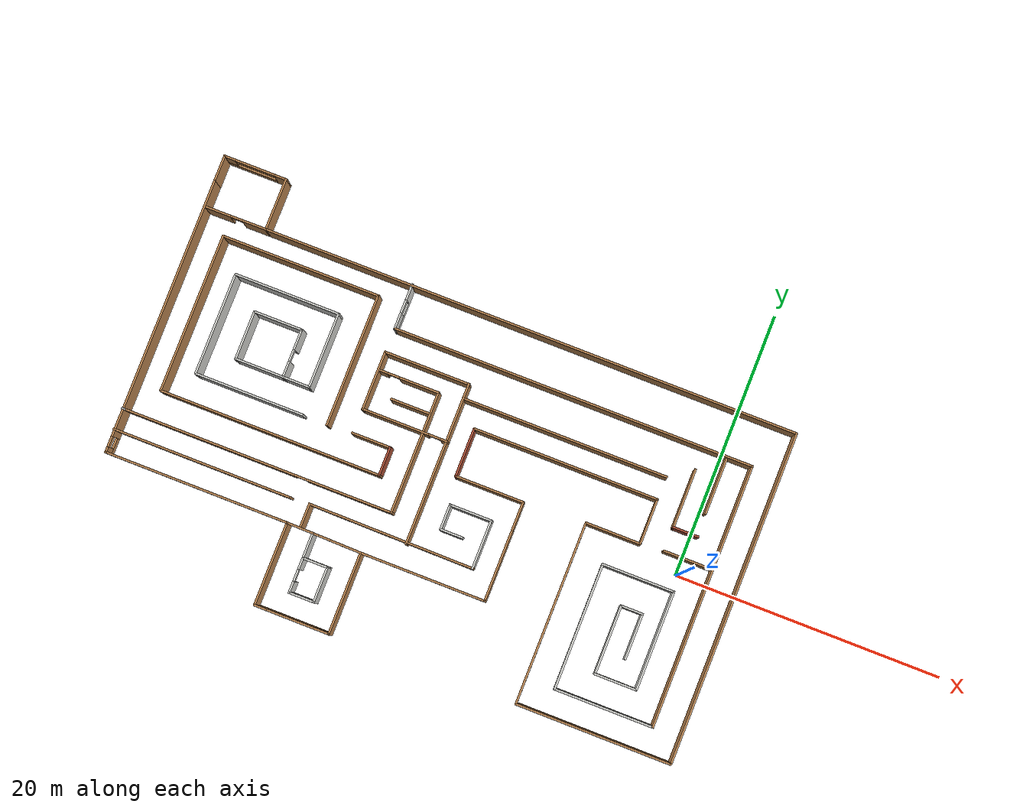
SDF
<?xml version='1.0'?>
<sdf version='1.6'>
  <model name='Building'>
    <pose frame=''>-18.2583 1.7119 0 0 -0 0</pose>
    <link name='Wall_0'>
      <pose frame=''>-22.4887 2.1266 0 0 0 -1.56733</pose>
      <visual name='Wall_0_Visual_0'>
        <pose frame=''>-0.641349 0 1.25 0 -0 0</pose>
        <geometry>
          <box>
            <size>19.6144 0.15 2.5</size>
          </box>
        </geometry>
        <material>
          <script>
            <uri>file://media/materials/scripts/gazebo.material</uri>
            <name>Gazebo/Wood</name>
          </script>
          <ambient>1 1 1 1</ambient>
        </material>
        <meta>
          <layer>0</layer>
        </meta>
      </visual>
      <collision name='Wall_0_Collision_0'>
        <geometry>
          <box>
            <size>19.6144 0.15 2.5</size>
          </box>
        </geometry>
        <pose frame=''>-0.641349 0 1.25 0 -0 0</pose>
      </collision>
      <visual name='Wall_0_Visual_1'>
        <pose frame=''>9.80721 0 0.4 0 -0 0</pose>
        <geometry>
          <box>
            <size>1.2827 0.15 0.8</size>
          </box>
        </geometry>
        <material>
          <script>
            <uri>file://media/materials/scripts/gazebo.material</uri>
            <name>Gazebo/Wood</name>
          </script>
          <ambient>1 1 1 1</ambient>
        </material>
        <meta>
          <layer>0</layer>
        </meta>
      </visual>
      <collision name='Wall_0_Collision_1'>
        <geometry>
          <box>
            <size>1.2827 0.15 0.8</size>
          </box>
        </geometry>
        <pose frame=''>9.80721 0 0.4 0 -0 0</pose>
      </collision>
      <visual name='Wall_0_Visual_2'>
        <pose frame=''>10.2072 0 1.65 0 -0 0</pose>
        <geometry>
          <box>
            <size>0.482698 0.15 1.7</size>
          </box>
        </geometry>
        <material>
          <script>
            <uri>file://media/materials/scripts/gazebo.material</uri>
            <name>Gazebo/Wood</name>
          </script>
          <ambient>1 1 1 1</ambient>
        </material>
        <meta>
          <layer>0</layer>
        </meta>
      </visual>
      <collision name='Wall_0_Collision_2'>
        <geometry>
          <box>
            <size>0.482698 0.15 1.7</size>
          </box>
        </geometry>
        <pose frame=''>10.2072 0 1.65 0 -0 0</pose>
      </collision>
      <visual name='Wall_0_Visual_3'>
        <pose frame=''>9.56587 0 2.15 0 -0 0</pose>
        <geometry>
          <box>
            <size>0.8 0.15 0.7</size>
          </box>
        </geometry>
        <material>
          <script>
            <uri>file://media/materials/scripts/gazebo.material</uri>
            <name>Gazebo/Wood</name>
          </script>
          <ambient>1 1 1 1</ambient>
        </material>
        <meta>
          <layer>0</layer>
        </meta>
      </visual>
      <collision name='Wall_0_Collision_3'>
        <geometry>
          <box>
            <size>0.8 0.15 0.7</size>
          </box>
        </geometry>
        <pose frame=''>9.56587 0 2.15 0 -0 0</pose>
      </collision>
    </link>
    <link name='Wall_1'>
      <collision name='Wall_1_Collision'>
        <geometry>
          <box>
            <size>13.928 0.15 2.5</size>
          </box>
        </geometry>
        <pose frame=''>0 0 1.25 0 -0 0</pose>
      </collision>
      <visual name='Wall_1_Visual'>
        <pose frame=''>0 0 1.25 0 -0 0</pose>
        <geometry>
          <box>
            <size>13.928 0.15 2.5</size>
          </box>
        </geometry>
        <material>
          <script>
            <uri>file://media/materials/scripts/gazebo.material</uri>
            <name>Gazebo/Wood</name>
          </script>
          <ambient>1 1 1 1</ambient>
        </material>
        <meta>
          <layer>0</layer>
        </meta>
      </visual>
      <pose frame=''>-15.5637 -8.2469 0 0 -0 0</pose>
    </link>
    <link name='Wall_10'>
      <collision name='Wall_10_Collision'>
        <geometry>
          <box>
            <size>14 0.15 2.5</size>
          </box>
        </geometry>
        <pose frame=''>0 0 1.25 0 -0 0</pose>
      </collision>
      <visual name='Wall_10_Visual'>
        <pose frame=''>0 0 1.25 0 -0 0</pose>
        <geometry>
          <box>
            <size>14 0.15 2.5</size>
          </box>
        </geometry>
        <material>
          <script>
            <uri>file://media/materials/scripts/gazebo.material</uri>
            <name>Gazebo/Wood</name>
          </script>
          <ambient>1 1 1 1</ambient>
        </material>
        <meta>
          <layer>0</layer>
        </meta>
      </visual>
      <pose frame=''>8.10018 2.69968 0 0 -0 0</pose>
    </link>
    <link name='Wall_11'>
      <collision name='Wall_11_Collision'>
        <geometry>
          <box>
            <size>3.5 0.15 2.5</size>
          </box>
        </geometry>
        <pose frame=''>0 0 1.25 0 -0 0</pose>
      </collision>
      <visual name='Wall_11_Visual'>
        <pose frame=''>0 0 1.25 0 -0 0</pose>
        <geometry>
          <box>
            <size>3.5 0.15 2.5</size>
          </box>
        </geometry>
        <material>
          <script>
            <uri>file://media/materials/scripts/gazebo.material</uri>
            <name>Gazebo/Wood</name>
          </script>
          <ambient>1 1 1 1</ambient>
        </material>
        <meta>
          <layer>0</layer>
        </meta>
      </visual>
      <pose frame=''>15.0252 1.02468 0 0 0 -1.5708</pose>
    </link>
    <link name='Wall_12'>
      <collision name='Wall_12_Collision'>
        <geometry>
          <box>
            <size>4.25 0.15 2.5</size>
          </box>
        </geometry>
        <pose frame=''>0 0 1.25 0 -0 0</pose>
      </collision>
      <visual name='Wall_12_Visual'>
        <pose frame=''>0 0 1.25 0 -0 0</pose>
        <geometry>
          <box>
            <size>4.25 0.15 2.5</size>
          </box>
        </geometry>
        <material>
          <script>
            <uri>file://media/materials/scripts/gazebo.material</uri>
            <name>Gazebo/Wood</name>
          </script>
          <ambient>1 1 1 1</ambient>
        </material>
        <meta>
          <layer>0</layer>
        </meta>
      </visual>
      <pose frame=''>12.9752 -0.650318 0 0 -0 3.14159</pose>
    </link>
    <link name='Wall_13'>
      <collision name='Wall_13_Collision'>
        <geometry>
          <box>
            <size>13.75 0.15 2.5</size>
          </box>
        </geometry>
        <pose frame=''>0 0 1.25 0 -0 0</pose>
      </collision>
      <visual name='Wall_13_Visual'>
        <pose frame=''>0 0 1.25 0 -0 0</pose>
        <geometry>
          <box>
            <size>13.75 0.15 2.5</size>
          </box>
        </geometry>
        <material>
          <script>
            <uri>file://media/materials/scripts/gazebo.material</uri>
            <name>Gazebo/Wood</name>
          </script>
          <ambient>1 1 1 1</ambient>
        </material>
        <meta>
          <layer>0</layer>
        </meta>
      </visual>
      <pose frame=''>10.9252 -7.45032 0 0 0 -1.5708</pose>
    </link>
    <link name='Wall_14'>
      <collision name='Wall_14_Collision'>
        <geometry>
          <box>
            <size>11.75 0.15 2.5</size>
          </box>
        </geometry>
        <pose frame=''>0 0 1.25 0 -0 0</pose>
      </collision>
      <visual name='Wall_14_Visual'>
        <pose frame=''>0 0 1.25 0 -0 0</pose>
        <geometry>
          <box>
            <size>11.75 0.15 2.5</size>
          </box>
        </geometry>
        <material>
          <script>
            <uri>file://media/materials/scripts/gazebo.material</uri>
            <name>Gazebo/Wood</name>
          </script>
          <ambient>1 1 1 1</ambient>
        </material>
        <meta>
          <layer>0</layer>
        </meta>
      </visual>
      <pose frame=''>16.7252 -14.2503 0 0 -0 0</pose>
    </link>
    <link name='Wall_15'>
      <collision name='Wall_15_Collision'>
        <geometry>
          <box>
            <size>25 0.15 2.5</size>
          </box>
        </geometry>
        <pose frame=''>0 0 1.25 0 -0 0</pose>
      </collision>
      <visual name='Wall_15_Visual'>
        <pose frame=''>0 0 1.25 0 -0 0</pose>
        <geometry>
          <box>
            <size>25 0.15 2.5</size>
          </box>
        </geometry>
        <material>
          <script>
            <uri>file://media/materials/scripts/gazebo.material</uri>
            <name>Gazebo/Wood</name>
          </script>
          <ambient>1 1 1 1</ambient>
        </material>
        <meta>
          <layer>0</layer>
        </meta>
      </visual>
      <pose frame=''>22.5252 -1.82532 0 0 -0 1.5708</pose>
    </link>
    <link name='Wall_16'>
      <collision name='Wall_16_Collision'>
        <geometry>
          <box>
            <size>40.5 0.15 2.5</size>
          </box>
        </geometry>
        <pose frame=''>0 0 1.25 0 -0 0</pose>
      </collision>
      <visual name='Wall_16_Visual'>
        <pose frame=''>0 0 1.25 0 -0 0</pose>
        <geometry>
          <box>
            <size>40.5 0.15 2.5</size>
          </box>
        </geometry>
        <material>
          <script>
            <uri>file://media/materials/scripts/gazebo.material</uri>
            <name>Gazebo/Wood</name>
          </script>
          <ambient>1 1 1 1</ambient>
        </material>
        <meta>
          <layer>0</layer>
        </meta>
      </visual>
      <pose frame=''>2.35024 10.5999 0 0 -0 3.14158</pose>
    </link>
    <link name='Wall_17'>
      <collision name='Wall_17_Collision'>
        <geometry>
          <box>
            <size>4 0.15 2.5</size>
          </box>
        </geometry>
        <pose frame=''>0 0 1.25 0 -0 0</pose>
      </collision>
      <visual name='Wall_17_Visual'>
        <pose frame=''>0 0 1.25 0 -0 0</pose>
        <geometry>
          <box>
            <size>4 0.15 2.5</size>
          </box>
        </geometry>
        <material>
          <script>
            <uri>file://media/materials/scripts/gazebo.material</uri>
            <name>Gazebo/Wood</name>
          </script>
          <ambient>1 1 1 1</ambient>
        </material>
        <meta>
          <layer>0</layer>
        </meta>
      </visual>
      <pose frame=''>-17.8248 12.5249 0 0 -0 1.57083</pose>
    </link>
    <link name='Wall_18'>
      <pose frame=''>-20.1748 14.4499 0 0 -0 3.1415</pose>
      <visual name='Wall_18_Visual_0'>
        <pose frame=''>-1.954 0 1.25 0 -0 0</pose>
        <geometry>
          <box>
            <size>0.941881 0.15 2.5</size>
          </box>
        </geometry>
        <material>
          <script>
            <uri>file://media/materials/scripts/gazebo.material</uri>
            <name>Gazebo/Wood</name>
          </script>
          <ambient>1 1 1 1</ambient>
        </material>
        <meta>
          <layer>0</layer>
        </meta>
      </visual>
      <collision name='Wall_18_Collision_0'>
        <geometry>
          <box>
            <size>0.941881 0.15 2.5</size>
          </box>
        </geometry>
        <pose frame=''>-1.954 0 1.25 0 -0 0</pose>
      </collision>
      <visual name='Wall_18_Visual_1'>
        <pose frame=''>0.470941 0 0.4 0 -0 0</pose>
        <geometry>
          <box>
            <size>3.908 0.15 0.8</size>
          </box>
        </geometry>
        <material>
          <script>
            <uri>file://media/materials/scripts/gazebo.material</uri>
            <name>Gazebo/Wood</name>
          </script>
          <ambient>1 1 1 1</ambient>
        </material>
        <meta>
          <layer>0</layer>
        </meta>
      </visual>
      <collision name='Wall_18_Collision_1'>
        <geometry>
          <box>
            <size>3.908 0.15 0.8</size>
          </box>
        </geometry>
        <pose frame=''>0.470941 0 0.4 0 -0 0</pose>
      </collision>
      <visual name='Wall_18_Visual_2'>
        <pose frame=''>1.97094 0 1.65 0 -0 0</pose>
        <geometry>
          <box>
            <size>0.907999 0.15 1.7</size>
          </box>
        </geometry>
        <material>
          <script>
            <uri>file://media/materials/scripts/gazebo.material</uri>
            <name>Gazebo/Wood</name>
          </script>
          <ambient>1 1 1 1</ambient>
        </material>
        <meta>
          <layer>0</layer>
        </meta>
      </visual>
      <collision name='Wall_18_Collision_2'>
        <geometry>
          <box>
            <size>0.907999 0.15 1.7</size>
          </box>
        </geometry>
        <pose frame=''>1.97094 0 1.65 0 -0 0</pose>
      </collision>
      <visual name='Wall_18_Visual_3'>
        <pose frame=''>0.016941 0 2.15 0 -0 0</pose>
        <geometry>
          <box>
            <size>3 0.15 0.7</size>
          </box>
        </geometry>
        <material>
          <script>
            <uri>file://media/materials/scripts/gazebo.material</uri>
            <name>Gazebo/Wood</name>
          </script>
          <ambient>1 1 1 1</ambient>
        </material>
        <meta>
          <layer>0</layer>
        </meta>
      </visual>
      <collision name='Wall_18_Collision_3'>
        <geometry>
          <box>
            <size>3 0.15 0.7</size>
          </box>
        </geometry>
        <pose frame=''>0.016941 0 2.15 0 -0 0</pose>
      </collision>
    </link>
    <link name='Wall_19'>
      <collision name='Wall_19_Collision'>
        <geometry>
          <box>
            <size>2.1 0.15 2.5</size>
          </box>
        </geometry>
        <pose frame=''>0 0 1.25 0 -0 0</pose>
      </collision>
      <visual name='Wall_19_Visual'>
        <pose frame=''>0 0 1.25 0 -0 0</pose>
        <geometry>
          <box>
            <size>2.1 0.15 2.5</size>
          </box>
        </geometry>
        <material>
          <script>
            <uri>file://media/materials/scripts/gazebo.material</uri>
            <name>Gazebo/Wood</name>
          </script>
          <ambient>0.921569 0.807843 0.615686 1</ambient>
        </material>
        <meta>
          <layer>0</layer>
        </meta>
      </visual>
      <pose frame=''>-22.5247 13.4751 0 0 0 -1.5708</pose>
    </link>
    <link name='Wall_2'>
      <collision name='Wall_2_Collision'>
        <geometry>
          <box>
            <size>6.35342 0.15 2.5</size>
          </box>
        </geometry>
        <pose frame=''>0 0 1.25 0 -0 0</pose>
      </collision>
      <visual name='Wall_2_Visual'>
        <pose frame=''>0 0 1.25 0 -0 0</pose>
        <geometry>
          <box>
            <size>6.35342 0.15 2.5</size>
          </box>
        </geometry>
        <material>
          <script>
            <uri>file://media/materials/scripts/gazebo.material</uri>
            <name>Gazebo/Wood</name>
          </script>
          <ambient>1 1 1 1</ambient>
        </material>
        <meta>
          <layer>0</layer>
        </meta>
      </visual>
      <pose frame=''>-8.6747 -11.3484 0 0 0 -1.5708</pose>
    </link>
    <link name='Wall_22'>
      <pose frame=''>-5.87476 -8.29861 0 0 -0 3.12313</pose>
      <visual name='Wall_22_Visual_0'>
        <pose frame=''>-1.68319 0 1.25 0 -0 0</pose>
        <geometry>
          <box>
            <size>2.38444 0.15 2.5</size>
          </box>
        </geometry>
        <material>
          <script>
            <uri>file://media/materials/scripts/gazebo.material</uri>
            <name>Gazebo/Wood</name>
          </script>
          <ambient>1 1 1 1</ambient>
        </material>
        <meta>
          <layer>0</layer>
        </meta>
      </visual>
      <collision name='Wall_22_Collision_0'>
        <geometry>
          <box>
            <size>2.38444 0.15 2.5</size>
          </box>
        </geometry>
        <pose frame=''>-1.68319 0 1.25 0 -0 0</pose>
      </collision>
      <visual name='Wall_22_Visual_1'>
        <pose frame=''>1.64222 0 1.25 0 -0 0</pose>
        <geometry>
          <box>
            <size>2.46639 0.15 2.5</size>
          </box>
        </geometry>
        <material>
          <script>
            <uri>file://media/materials/scripts/gazebo.material</uri>
            <name>Gazebo/Wood</name>
          </script>
          <ambient>1 1 1 1</ambient>
        </material>
        <meta>
          <layer>0</layer>
        </meta>
      </visual>
      <collision name='Wall_22_Collision_1'>
        <geometry>
          <box>
            <size>2.46639 0.15 2.5</size>
          </box>
        </geometry>
        <pose frame=''>1.64222 0 1.25 0 -0 0</pose>
      </collision>
      <visual name='Wall_22_Visual_2'>
        <pose frame=''>-0.040973 0 2.25 0 -0 0</pose>
        <geometry>
          <box>
            <size>0.9 0.15 0.5</size>
          </box>
        </geometry>
        <material>
          <script>
            <uri>file://media/materials/scripts/gazebo.material</uri>
            <name>Gazebo/Wood</name>
          </script>
          <ambient>1 1 1 1</ambient>
        </material>
        <meta>
          <layer>0</layer>
        </meta>
      </visual>
      <collision name='Wall_22_Collision_2'>
        <geometry>
          <box>
            <size>0.9 0.15 0.5</size>
          </box>
        </geometry>
        <pose frame=''>-0.040973 0 2.25 0 -0 0</pose>
      </collision>
    </link>
    <link name='Wall_24'>
      <collision name='Wall_24_Collision'>
        <geometry>
          <box>
            <size>2 0.15 2.5</size>
          </box>
        </geometry>
        <pose frame=''>0 0 1.25 0 -0 0</pose>
      </collision>
      <visual name='Wall_24_Visual'>
        <pose frame=''>0 0 1.25 0 -0 0</pose>
        <geometry>
          <box>
            <size>2 0.15 2.5</size>
          </box>
        </geometry>
        <material>
          <script>
            <uri>file://media/materials/scripts/gazebo.material</uri>
            <name>Gazebo/CeilingTiled</name>
          </script>
          <ambient>1 1 1 1</ambient>
        </material>
        <meta>
          <layer>0</layer>
        </meta>
      </visual>
      <pose frame=''>-6.7275 -9.22377 0 0 0 -1.57101</pose>
    </link>
    <link name='Wall_25'>
      <collision name='Wall_25_Collision'>
        <geometry>
          <box>
            <size>2 0.15 2.5</size>
          </box>
        </geometry>
        <pose frame=''>0 0 1.25 0 -0 0</pose>
      </collision>
      <visual name='Wall_25_Visual'>
        <pose frame=''>0 0 1.25 0 -0 0</pose>
        <geometry>
          <box>
            <size>2 0.15 2.5</size>
          </box>
        </geometry>
        <material>
          <script>
            <uri>file://media/materials/scripts/gazebo.material</uri>
            <name>Gazebo/CeilingTiled</name>
          </script>
          <ambient>1 1 1 1</ambient>
        </material>
        <meta>
          <layer>0</layer>
        </meta>
      </visual>
      <pose frame=''>-5.8027 -10.1489 0 0 -0 0</pose>
    </link>
    <link name='Wall_27'>
      <collision name='Wall_27_Collision'>
        <geometry>
          <box>
            <size>2.75 0.15 2.5</size>
          </box>
        </geometry>
        <pose frame=''>0 0 1.25 0 -0 0</pose>
      </collision>
      <visual name='Wall_27_Visual'>
        <pose frame=''>0 0 1.25 0 -0 0</pose>
        <geometry>
          <box>
            <size>2.75 0.15 2.5</size>
          </box>
        </geometry>
        <material>
          <script>
            <uri>file://media/materials/scripts/gazebo.material</uri>
            <name>Gazebo/CeilingTiled</name>
          </script>
          <ambient>1 1 1 1</ambient>
        </material>
        <meta>
          <layer>0</layer>
        </meta>
      </visual>
      <pose frame=''>-4.8775 -11.4488 0 0 0 -1.57064</pose>
    </link>
    <link name='Wall_28'>
      <collision name='Wall_28_Collision'>
        <geometry>
          <box>
            <size>2.0004 0.15 2.5</size>
          </box>
        </geometry>
        <pose frame=''>0 0 1.25 0 -0 0</pose>
      </collision>
      <visual name='Wall_28_Visual'>
        <pose frame=''>0 0 1.25 0 -0 0</pose>
        <geometry>
          <box>
            <size>2.0004 0.15 2.5</size>
          </box>
        </geometry>
        <material>
          <script>
            <uri>file://media/materials/scripts/gazebo.material</uri>
            <name>Gazebo/CeilingTiled</name>
          </script>
          <ambient>1 1 1 1</ambient>
        </material>
        <meta>
          <layer>0</layer>
        </meta>
      </visual>
      <pose frame=''>-5.8025 -12.7488 0 0 0 -3.14146</pose>
    </link>
    <link name='Wall_29'>
      <pose frame=''>-6.7277 -11.4489 0 0 -0 1.5708</pose>
      <visual name='Wall_29_Visual_0'>
        <pose frame=''>-0.915206 0 1.25 0 -0 0</pose>
        <geometry>
          <box>
            <size>0.919835 0.15 2.5</size>
          </box>
        </geometry>
        <material>
          <script>
            <uri>file://media/materials/scripts/gazebo.material</uri>
            <name>Gazebo/CeilingTiled</name>
          </script>
          <ambient>1 1 1 1</ambient>
        </material>
        <meta>
          <layer>0</layer>
        </meta>
      </visual>
      <collision name='Wall_29_Collision_0'>
        <geometry>
          <box>
            <size>0.919835 0.15 2.5</size>
          </box>
        </geometry>
        <pose frame=''>-0.915206 0 1.25 0 -0 0</pose>
      </collision>
      <visual name='Wall_29_Visual_1'>
        <pose frame=''>0.909917 0 1.25 0 -0 0</pose>
        <geometry>
          <box>
            <size>0.930411 0.15 2.5</size>
          </box>
        </geometry>
        <material>
          <script>
            <uri>file://media/materials/scripts/gazebo.material</uri>
            <name>Gazebo/CeilingTiled</name>
          </script>
          <ambient>1 1 1 1</ambient>
        </material>
        <meta>
          <layer>0</layer>
        </meta>
      </visual>
      <collision name='Wall_29_Collision_1'>
        <geometry>
          <box>
            <size>0.930411 0.15 2.5</size>
          </box>
        </geometry>
        <pose frame=''>0.909917 0 1.25 0 -0 0</pose>
      </collision>
      <visual name='Wall_29_Visual_2'>
        <pose frame=''>-0.005288 0 2.25 0 -0 0</pose>
        <geometry>
          <box>
            <size>0.9 0.15 0.5</size>
          </box>
        </geometry>
        <material>
          <script>
            <uri>file://media/materials/scripts/gazebo.material</uri>
            <name>Gazebo/CeilingTiled</name>
          </script>
          <ambient>1 1 1 1</ambient>
        </material>
        <meta>
          <layer>0</layer>
        </meta>
      </visual>
      <collision name='Wall_29_Collision_2'>
        <geometry>
          <box>
            <size>0.9 0.15 0.5</size>
          </box>
        </geometry>
        <pose frame=''>-0.005288 0 2.25 0 -0 0</pose>
      </collision>
    </link>
    <link name='Wall_3'>
      <pose frame=''>-5.8747 -14.4499 0 0 -0 0</pose>
      <visual name='Wall_3_Visual_0'>
        <pose frame=''>-2.37464 0 1.25 0 -0 0</pose>
        <geometry>
          <box>
            <size>1.00072 0.15 2.5</size>
          </box>
        </geometry>
        <material>
          <script>
            <uri>file://media/materials/scripts/gazebo.material</uri>
            <name>Gazebo/Wood</name>
          </script>
          <ambient>1 1 1 1</ambient>
        </material>
        <meta>
          <layer>0</layer>
        </meta>
      </visual>
      <collision name='Wall_3_Collision_0'>
        <geometry>
          <box>
            <size>1.00072 0.15 2.5</size>
          </box>
        </geometry>
        <pose frame=''>-2.37464 0 1.25 0 -0 0</pose>
      </collision>
      <visual name='Wall_3_Visual_1'>
        <pose frame=''>0.50036 0 0.4 0 -0 0</pose>
        <geometry>
          <box>
            <size>4.74928 0.15 0.8</size>
          </box>
        </geometry>
        <material>
          <script>
            <uri>file://media/materials/scripts/gazebo.material</uri>
            <name>Gazebo/Wood</name>
          </script>
          <ambient>1 1 1 1</ambient>
        </material>
        <meta>
          <layer>0</layer>
        </meta>
      </visual>
      <collision name='Wall_3_Collision_1'>
        <geometry>
          <box>
            <size>4.74928 0.15 0.8</size>
          </box>
        </geometry>
        <pose frame=''>0.50036 0 0.4 0 -0 0</pose>
      </collision>
      <visual name='Wall_3_Visual_2'>
        <pose frame=''>2.25036 0 1.65 0 -0 0</pose>
        <geometry>
          <box>
            <size>1.24928 0.15 1.7</size>
          </box>
        </geometry>
        <material>
          <script>
            <uri>file://media/materials/scripts/gazebo.material</uri>
            <name>Gazebo/Wood</name>
          </script>
          <ambient>1 1 1 1</ambient>
        </material>
        <meta>
          <layer>0</layer>
        </meta>
      </visual>
      <collision name='Wall_3_Collision_2'>
        <geometry>
          <box>
            <size>1.24928 0.15 1.7</size>
          </box>
        </geometry>
        <pose frame=''>2.25036 0 1.65 0 -0 0</pose>
      </collision>
      <visual name='Wall_3_Visual_3'>
        <pose frame=''>-0.124281 0 2.15 0 -0 0</pose>
        <geometry>
          <box>
            <size>3.5 0.15 0.7</size>
          </box>
        </geometry>
        <material>
          <script>
            <uri>file://media/materials/scripts/gazebo.material</uri>
            <name>Gazebo/Wood</name>
          </script>
          <ambient>1 1 1 1</ambient>
        </material>
        <meta>
          <layer>0</layer>
        </meta>
      </visual>
      <collision name='Wall_3_Collision_3'>
        <geometry>
          <box>
            <size>3.5 0.15 0.7</size>
          </box>
        </geometry>
        <pose frame=''>-0.124281 0 2.15 0 -0 0</pose>
      </collision>
    </link>
    <link name='Wall_31'>
      <collision name='Wall_31_Collision'>
        <geometry>
          <box>
            <size>1.94917 0.15 2.5</size>
          </box>
        </geometry>
        <pose frame=''>0 0 1.25 0 -0 0</pose>
      </collision>
      <visual name='Wall_31_Visual'>
        <pose frame=''>0 0 1.25 0 -0 0</pose>
        <geometry>
          <box>
            <size>1.94917 0.15 2.5</size>
          </box>
        </geometry>
        <material>
          <script>
            <uri>file://media/materials/scripts/gazebo.material</uri>
            <name>Gazebo/Wood</name>
          </script>
          <ambient>1 1 1 1</ambient>
        </material>
        <meta>
          <layer>0</layer>
        </meta>
      </visual>
      <pose frame=''>-7.6987 -7.3474 0 0 -0 1.5708</pose>
    </link>
    <link name='Wall_32'>
      <collision name='Wall_32_Collision'>
        <geometry>
          <box>
            <size>12.5011 0.15 2.5</size>
          </box>
        </geometry>
        <pose frame=''>0 0 1.25 0 -0 0</pose>
      </collision>
      <visual name='Wall_32_Visual'>
        <pose frame=''>0 0 1.25 0 -0 0</pose>
        <geometry>
          <box>
            <size>12.5011 0.15 2.5</size>
          </box>
        </geometry>
        <material>
          <script>
            <uri>file://media/materials/scripts/gazebo.material</uri>
            <name>Gazebo/Wood</name>
          </script>
          <ambient>1 1 1 1</ambient>
        </material>
        <meta>
          <layer>0</layer>
        </meta>
      </visual>
      <pose frame=''>-1.52347 -6.48873 0 0 0 -0.006612</pose>
    </link>
    <link name='Wall_33'>
      <collision name='Wall_33_Collision'>
        <geometry>
          <box>
            <size>3.75 0.15 2.5</size>
          </box>
        </geometry>
        <pose frame=''>0 0 1.25 0 -0 0</pose>
      </collision>
      <visual name='Wall_33_Visual'>
        <pose frame=''>0 0 1.25 0 -0 0</pose>
        <geometry>
          <box>
            <size>3.75 0.15 2.5</size>
          </box>
        </geometry>
        <material>
          <script>
            <uri>file://media/materials/scripts/gazebo.material</uri>
            <name>Gazebo/CeilingTiled</name>
          </script>
          <ambient>1 1 1 1</ambient>
        </material>
        <meta>
          <layer>0</layer>
        </meta>
      </visual>
      <pose frame=''>4.65177 -4.72956 0 0 -0 1.5708</pose>
    </link>
    <link name='Wall_34'>
      <collision name='Wall_34_Collision'>
        <geometry>
          <box>
            <size>3.25 0.15 2.5</size>
          </box>
        </geometry>
        <pose frame=''>0 0 1.25 0 -0 0</pose>
      </collision>
      <visual name='Wall_34_Visual'>
        <pose frame=''>0 0 1.25 0 -0 0</pose>
        <geometry>
          <box>
            <size>3.25 0.15 2.5</size>
          </box>
        </geometry>
        <material>
          <script>
            <uri>file://media/materials/scripts/gazebo.material</uri>
            <name>Gazebo/CeilingTiled</name>
          </script>
          <ambient>1 1 1 1</ambient>
        </material>
        <meta>
          <layer>0</layer>
        </meta>
      </visual>
      <pose frame=''>3.10177 -2.92956 0 0 -0 3.14159</pose>
    </link>
    <link name='Wall_35'>
      <collision name='Wall_35_Collision'>
        <geometry>
          <box>
            <size>2 0.15 2.5</size>
          </box>
        </geometry>
        <pose frame=''>0 0 1.25 0 -0 0</pose>
      </collision>
      <visual name='Wall_35_Visual'>
        <pose frame=''>0 0 1.25 0 -0 0</pose>
        <geometry>
          <box>
            <size>2 0.15 2.5</size>
          </box>
        </geometry>
        <material>
          <script>
            <uri>file://media/materials/scripts/gazebo.material</uri>
            <name>Gazebo/CeilingTiled</name>
          </script>
          <ambient>1 1 1 1</ambient>
        </material>
        <meta>
          <layer>0</layer>
        </meta>
      </visual>
      <pose frame=''>1.55177 -3.85456 0 0 0 -1.5708</pose>
    </link>
    <link name='Wall_36'>
      <collision name='Wall_36_Collision'>
        <geometry>
          <box>
            <size>1.75 0.15 2.5</size>
          </box>
        </geometry>
        <pose frame=''>0 0 1.25 0 -0 0</pose>
      </collision>
      <visual name='Wall_36_Visual'>
        <pose frame=''>0 0 1.25 0 -0 0</pose>
        <geometry>
          <box>
            <size>1.75 0.15 2.5</size>
          </box>
        </geometry>
        <material>
          <script>
            <uri>file://media/materials/scripts/gazebo.material</uri>
            <name>Gazebo/CeilingTiled</name>
          </script>
          <ambient>1 1 1 1</ambient>
        </material>
        <meta>
          <layer>0</layer>
        </meta>
      </visual>
      <pose frame=''>2.35177 -4.77956 0 0 -0 0</pose>
    </link>
    <link name='Wall_38'>
      <collision name='Wall_38_Collision'>
        <geometry>
          <box>
            <size>12.25 0.15 2.5</size>
          </box>
        </geometry>
        <pose frame=''>0 0 1.25 0 -0 0</pose>
      </collision>
      <visual name='Wall_38_Visual'>
        <pose frame=''>0 0 1.25 0 -0 0</pose>
        <geometry>
          <box>
            <size>12.25 0.15 2.5</size>
          </box>
        </geometry>
        <material>
          <script>
            <uri>file://media/materials/scripts/gazebo.material</uri>
            <name>Gazebo/Wood</name>
          </script>
          <ambient>1 1 1 1</ambient>
        </material>
        <meta>
          <layer>0</layer>
        </meta>
      </visual>
      <pose frame=''>-0.3357 -0.549898 0 0 -0 1.5708</pose>
    </link>
    <link name='Wall_39'>
      <collision name='Wall_39_Collision'>
        <geometry>
          <box>
            <size>6.5 0.15 2.5</size>
          </box>
        </geometry>
        <pose frame=''>0 0 1.25 0 -0 0</pose>
      </collision>
      <visual name='Wall_39_Visual'>
        <pose frame=''>0 0 1.25 0 -0 0</pose>
        <geometry>
          <box>
            <size>6.5 0.15 2.5</size>
          </box>
        </geometry>
        <material>
          <script>
            <uri>file://media/materials/scripts/gazebo.material</uri>
            <name>Gazebo/Wood</name>
          </script>
          <ambient>1 1 1 1</ambient>
        </material>
        <meta>
          <layer>0</layer>
        </meta>
      </visual>
      <pose frame=''>-3.51051 5.50029 0 0 -0 3.14153</pose>
    </link>
    <link name='Wall_4'>
      <collision name='Wall_4_Collision'>
        <geometry>
          <box>
            <size>6.25 0.15 2.5</size>
          </box>
        </geometry>
        <pose frame=''>0 0 1.25 0 -0 0</pose>
      </collision>
      <visual name='Wall_4_Visual'>
        <pose frame=''>0 0 1.25 0 -0 0</pose>
        <geometry>
          <box>
            <size>6.25 0.15 2.5</size>
          </box>
        </geometry>
        <material>
          <script>
            <uri>file://media/materials/scripts/gazebo.material</uri>
            <name>Gazebo/Wood</name>
          </script>
          <ambient>1 1 1 1</ambient>
        </material>
        <meta>
          <layer>0</layer>
        </meta>
      </visual>
      <pose frame=''>-3.07476 -11.4001 0 0 -0 1.57082</pose>
    </link>
    <link name='Wall_40'>
      <collision name='Wall_40_Collision'>
        <geometry>
          <box>
            <size>4.5 0.15 2.5</size>
          </box>
        </geometry>
        <pose frame=''>0 0 1.25 0 -0 0</pose>
      </collision>
      <visual name='Wall_40_Visual'>
        <pose frame=''>0 0 1.25 0 -0 0</pose>
        <geometry>
          <box>
            <size>4.5 0.15 2.5</size>
          </box>
        </geometry>
        <material>
          <script>
            <uri>file://media/materials/scripts/gazebo.material</uri>
            <name>Gazebo/Wood</name>
          </script>
          <ambient>1 1 1 1</ambient>
        </material>
        <meta>
          <layer>0</layer>
        </meta>
      </visual>
      <pose frame=''>-6.68532 3.32548 0 0 0 -1.5708</pose>
    </link>
    <link name='Wall_41'>
      <pose frame=''>-3.51032 1.15048 0 0 -0 0</pose>
      <visual name='Wall_41_Visual_0'>
        <pose frame=''>-0.707511 0 1.25 0 -0 0</pose>
        <geometry>
          <box>
            <size>5.08498 0.15 2.5</size>
          </box>
        </geometry>
        <material>
          <script>
            <uri>file://media/materials/scripts/gazebo.material</uri>
            <name>Gazebo/Wood</name>
          </script>
          <ambient>1 1 1 1</ambient>
        </material>
        <meta>
          <layer>0</layer>
        </meta>
      </visual>
      <collision name='Wall_41_Collision_0'>
        <geometry>
          <box>
            <size>5.08498 0.15 2.5</size>
          </box>
        </geometry>
        <pose frame=''>-0.707511 0 1.25 0 -0 0</pose>
      </collision>
      <visual name='Wall_41_Visual_1'>
        <pose frame=''>2.99249 0 1.25 0 -0 0</pose>
        <geometry>
          <box>
            <size>0.515021 0.15 2.5</size>
          </box>
        </geometry>
        <material>
          <script>
            <uri>file://media/materials/scripts/gazebo.material</uri>
            <name>Gazebo/Wood</name>
          </script>
          <ambient>1 1 1 1</ambient>
        </material>
        <meta>
          <layer>0</layer>
        </meta>
      </visual>
      <collision name='Wall_41_Collision_1'>
        <geometry>
          <box>
            <size>0.515021 0.15 2.5</size>
          </box>
        </geometry>
        <pose frame=''>2.99249 0 1.25 0 -0 0</pose>
      </collision>
      <visual name='Wall_41_Visual_2'>
        <pose frame=''>2.28498 0 2.25 0 -0 0</pose>
        <geometry>
          <box>
            <size>0.9 0.15 0.5</size>
          </box>
        </geometry>
        <material>
          <script>
            <uri>file://media/materials/scripts/gazebo.material</uri>
            <name>Gazebo/Wood</name>
          </script>
          <ambient>1 1 1 1</ambient>
        </material>
        <meta>
          <layer>0</layer>
        </meta>
      </visual>
      <collision name='Wall_41_Collision_2'>
        <geometry>
          <box>
            <size>0.9 0.15 0.5</size>
          </box>
        </geometry>
        <pose frame=''>2.28498 0 2.25 0 -0 0</pose>
      </collision>
    </link>
    <link name='Wall_43'>
      <collision name='Wall_43_Collision'>
        <geometry>
          <box>
            <size>9.25 0.15 2.5</size>
          </box>
        </geometry>
        <pose frame=''>0 0 1.25 0 -0 0</pose>
      </collision>
      <visual name='Wall_43_Visual'>
        <pose frame=''>0 0 1.25 0 -0 0</pose>
        <geometry>
          <box>
            <size>9.25 0.15 2.5</size>
          </box>
        </geometry>
        <material>
          <script>
            <uri>file://media/materials/scripts/gazebo.material</uri>
            <name>Gazebo/Wood</name>
          </script>
          <ambient>1 1 1 1</ambient>
        </material>
        <meta>
          <layer>0</layer>
        </meta>
      </visual>
      <pose frame=''>-2.1157 -0.387898 0 0 0 -1.5708</pose>
    </link>
    <link name='Wall_44'>
      <pose frame=''>-12.3202 -4.9379 0 0 -0 3.14159</pose>
      <visual name='Wall_44_Visual_0'>
        <pose frame=''>-7.02658 0 1.25 0 -0 0</pose>
        <geometry>
          <box>
            <size>6.50584 0.15 2.5</size>
          </box>
        </geometry>
        <material>
          <script>
            <uri>file://media/materials/scripts/gazebo.material</uri>
            <name>Gazebo/Wood</name>
          </script>
          <ambient>1 1 1 1</ambient>
        </material>
        <meta>
          <layer>0</layer>
        </meta>
      </visual>
      <collision name='Wall_44_Collision_0'>
        <geometry>
          <box>
            <size>6.50584 0.15 2.5</size>
          </box>
        </geometry>
        <pose frame=''>-7.02658 0 1.25 0 -0 0</pose>
      </collision>
      <visual name='Wall_44_Visual_1'>
        <pose frame=''>3.70292 0 1.25 0 -0 0</pose>
        <geometry>
          <box>
            <size>13.1532 0.15 2.5</size>
          </box>
        </geometry>
        <material>
          <script>
            <uri>file://media/materials/scripts/gazebo.material</uri>
            <name>Gazebo/Wood</name>
          </script>
          <ambient>1 1 1 1</ambient>
        </material>
        <meta>
          <layer>0</layer>
        </meta>
      </visual>
      <collision name='Wall_44_Collision_1'>
        <geometry>
          <box>
            <size>13.1532 0.15 2.5</size>
          </box>
        </geometry>
        <pose frame=''>3.70292 0 1.25 0 -0 0</pose>
      </collision>
      <visual name='Wall_44_Visual_2'>
        <pose frame=''>-3.32366 0 2.25 0 -0 0</pose>
        <geometry>
          <box>
            <size>0.9 0.15 0.5</size>
          </box>
        </geometry>
        <material>
          <script>
            <uri>file://media/materials/scripts/gazebo.material</uri>
            <name>Gazebo/Wood</name>
          </script>
          <ambient>1 1 1 1</ambient>
        </material>
        <meta>
          <layer>0</layer>
        </meta>
      </visual>
      <collision name='Wall_44_Collision_2'>
        <geometry>
          <box>
            <size>0.9 0.15 0.5</size>
          </box>
        </geometry>
        <pose frame=''>-3.32366 0 2.25 0 -0 0</pose>
      </collision>
    </link>
    <link name='Wall_45'>
      <collision name='Wall_45_Collision'>
        <geometry>
          <box>
            <size>0.359336 0.15 2.5</size>
          </box>
        </geometry>
        <pose frame=''>0 0 1.25 0 -0 0</pose>
      </collision>
      <visual name='Wall_45_Visual'>
        <pose frame=''>0 0 1.25 0 -0 0</pose>
        <geometry>
          <box>
            <size>0.359336 0.15 2.5</size>
          </box>
        </geometry>
        <material>
          <script>
            <uri>file://media/materials/scripts/gazebo.material</uri>
            <name>Gazebo/Grey</name>
          </script>
          <ambient>1 1 1 1</ambient>
        </material>
        <meta>
          <layer>0</layer>
        </meta>
      </visual>
      <pose frame=''>-22.42 -4.93812 0 0 0 -0.002083</pose>
    </link>
    <link name='Wall_47'>
      <collision name='Wall_47_Collision'>
        <geometry>
          <box>
            <size>3 0.15 2.5</size>
          </box>
        </geometry>
        <pose frame=''>0 0 1.25 0 -0 0</pose>
      </collision>
      <visual name='Wall_47_Visual'>
        <pose frame=''>0 0 1.25 0 -0 0</pose>
        <geometry>
          <box>
            <size>3 0.15 2.5</size>
          </box>
        </geometry>
        <material>
          <script>
            <uri>file://media/materials/scripts/gazebo.material</uri>
            <name>Gazebo/Wood</name>
          </script>
          <ambient>1 1 1 1</ambient>
        </material>
        <meta>
          <layer>0</layer>
        </meta>
      </visual>
      <pose frame=''>-3.60317 2.54344 0 0 -0 0</pose>
    </link>
    <link name='Wall_5'>
      <collision name='Wall_5_Collision'>
        <geometry>
          <box>
            <size>9.5 0.15 2.5</size>
          </box>
        </geometry>
        <pose frame=''>0 0 1.25 0 -0 0</pose>
      </collision>
      <visual name='Wall_5_Visual'>
        <pose frame=''>0 0 1.25 0 -0 0</pose>
        <geometry>
          <box>
            <size>9.5 0.15 2.5</size>
          </box>
        </geometry>
        <material>
          <script>
            <uri>file://media/materials/scripts/gazebo.material</uri>
            <name>Gazebo/Wood</name>
          </script>
          <ambient>1 1 1 1</ambient>
        </material>
        <meta>
          <layer>0</layer>
        </meta>
      </visual>
      <pose frame=''>1.60018 -8.35032 0 0 -0 0</pose>
    </link>
    <link name='Wall_50'>
      <pose frame=''>-4.4007 4.1621 0 0 -0 3.14159</pose>
      <visual name='Wall_50_Visual_0'>
        <pose frame=''>-0.848534 0 1.25 0 -0 0</pose>
        <geometry>
          <box>
            <size>3.02293 0.15 2.5</size>
          </box>
        </geometry>
        <material>
          <script>
            <uri>file://media/materials/scripts/gazebo.material</uri>
            <name>Gazebo/Wood</name>
          </script>
          <ambient>1 1 1 1</ambient>
        </material>
        <meta>
          <layer>0</layer>
        </meta>
      </visual>
      <collision name='Wall_50_Collision_0'>
        <geometry>
          <box>
            <size>3.02293 0.15 2.5</size>
          </box>
        </geometry>
        <pose frame=''>-0.848534 0 1.25 0 -0 0</pose>
      </collision>
      <visual name='Wall_50_Visual_1'>
        <pose frame=''>1.96147 0 1.25 0 -0 0</pose>
        <geometry>
          <box>
            <size>0.797068 0.15 2.5</size>
          </box>
        </geometry>
        <material>
          <script>
            <uri>file://media/materials/scripts/gazebo.material</uri>
            <name>Gazebo/Wood</name>
          </script>
          <ambient>1 1 1 1</ambient>
        </material>
        <meta>
          <layer>0</layer>
        </meta>
      </visual>
      <collision name='Wall_50_Collision_1'>
        <geometry>
          <box>
            <size>0.797068 0.15 2.5</size>
          </box>
        </geometry>
        <pose frame=''>1.96147 0 1.25 0 -0 0</pose>
      </collision>
      <visual name='Wall_50_Visual_2'>
        <pose frame=''>1.11293 0 2.25 0 -0 0</pose>
        <geometry>
          <box>
            <size>0.9 0.15 0.5</size>
          </box>
        </geometry>
        <material>
          <script>
            <uri>file://media/materials/scripts/gazebo.material</uri>
            <name>Gazebo/Wood</name>
          </script>
          <ambient>1 1 1 1</ambient>
        </material>
        <meta>
          <layer>0</layer>
        </meta>
      </visual>
      <collision name='Wall_50_Collision_2'>
        <geometry>
          <box>
            <size>0.9 0.15 0.5</size>
          </box>
        </geometry>
        <pose frame=''>1.11293 0 2.25 0 -0 0</pose>
      </collision>
    </link>
    <link name='Wall_52'>
      <collision name='Wall_52_Collision'>
        <geometry>
          <box>
            <size>13.439 0.15 2.5</size>
          </box>
        </geometry>
        <pose frame=''>0 0 1.25 0 -0 0</pose>
      </collision>
      <visual name='Wall_52_Visual'>
        <pose frame=''>0 0 1.25 0 -0 0</pose>
        <geometry>
          <box>
            <size>13.439 0.15 2.5</size>
          </box>
        </geometry>
        <material>
          <script>
            <uri>file://media/materials/scripts/gazebo.material</uri>
            <name>Gazebo/Wood</name>
          </script>
          <ambient>1 1 1 1</ambient>
        </material>
        <meta>
          <layer>0</layer>
        </meta>
      </visual>
      <pose frame=''>-15.8802 -6.5189 0 0 -0 3.14159</pose>
    </link>
    <link name='Wall_54'>
      <collision name='Wall_54_Collision'>
        <geometry>
          <box>
            <size>3 0.15 2.5</size>
          </box>
        </geometry>
        <pose frame=''>0 0 1.25 0 -0 0</pose>
      </collision>
      <visual name='Wall_54_Visual'>
        <pose frame=''>0 0 1.25 0 -0 0</pose>
        <geometry>
          <box>
            <size>3 0.15 2.5</size>
          </box>
        </geometry>
        <material>
          <script>
            <uri>file://media/materials/scripts/gazebo.material</uri>
            <name>Gazebo/Wood</name>
          </script>
          <ambient>1 1 1 1</ambient>
        </material>
        <meta>
          <layer>0</layer>
        </meta>
      </visual>
      <pose frame=''>-5.3023 -0.693004 0 0 -0 0</pose>
    </link>
    <link name='Wall_55'>
      <collision name='Wall_55_Collision'>
        <geometry>
          <box>
            <size>2.25 0.15 2.5</size>
          </box>
        </geometry>
        <pose frame=''>0 0 1.25 0 -0 0</pose>
      </collision>
      <visual name='Wall_55_Visual'>
        <pose frame=''>0 0 1.25 0 -0 0</pose>
        <geometry>
          <box>
            <size>2.25 0.15 2.5</size>
          </box>
        </geometry>
        <material>
          <script>
            <uri>file://media/materials/scripts/gazebo.material</uri>
            <name>Gazebo/Bricks</name>
          </script>
          <ambient>1 1 1 1</ambient>
        </material>
        <meta>
          <layer>0</layer>
        </meta>
      </visual>
      <pose frame=''>-3.8773 -1.743 0 0 0 -1.5708</pose>
    </link>
    <link name='Wall_56'>
      <collision name='Wall_56_Collision'>
        <geometry>
          <box>
            <size>16.75 0.15 2.5</size>
          </box>
        </geometry>
        <pose frame=''>0 0 1.25 0 -0 0</pose>
      </collision>
      <visual name='Wall_56_Visual'>
        <pose frame=''>0 0 1.25 0 -0 0</pose>
        <geometry>
          <box>
            <size>16.75 0.15 2.5</size>
          </box>
        </geometry>
        <material>
          <script>
            <uri>file://media/materials/scripts/gazebo.material</uri>
            <name>Gazebo/Wood</name>
          </script>
          <ambient>1 1 1 1</ambient>
        </material>
        <meta>
          <layer>0</layer>
        </meta>
      </visual>
      <pose frame=''>-12.1773 -2.793 0 0 -0 3.14159</pose>
    </link>
    <link name='Wall_57'>
      <collision name='Wall_57_Collision'>
        <geometry>
          <box>
            <size>12 0.15 2.5</size>
          </box>
        </geometry>
        <pose frame=''>0 0 1.25 0 -0 0</pose>
      </collision>
      <visual name='Wall_57_Visual'>
        <pose frame=''>0 0 1.25 0 -0 0</pose>
        <geometry>
          <box>
            <size>12 0.15 2.5</size>
          </box>
        </geometry>
        <material>
          <script>
            <uri>file://media/materials/scripts/gazebo.material</uri>
            <name>Gazebo/Wood</name>
          </script>
          <ambient>1 1 1 1</ambient>
        </material>
        <meta>
          <layer>0</layer>
        </meta>
      </visual>
      <pose frame=''>-20.4773 3.132 0 0 -0 1.5708</pose>
    </link>
    <link name='Wall_58'>
      <collision name='Wall_58_Collision'>
        <geometry>
          <box>
            <size>12 0.15 2.5</size>
          </box>
        </geometry>
        <pose frame=''>0 0 1.25 0 -0 0</pose>
      </collision>
      <visual name='Wall_58_Visual'>
        <pose frame=''>0 0 1.25 0 -0 0</pose>
        <geometry>
          <box>
            <size>12 0.15 2.5</size>
          </box>
        </geometry>
        <material>
          <script>
            <uri>file://media/materials/scripts/gazebo.material</uri>
            <name>Gazebo/Wood</name>
          </script>
          <ambient>1 1 1 1</ambient>
        </material>
        <meta>
          <layer>0</layer>
        </meta>
      </visual>
      <pose frame=''>-14.5523 9.057 0 0 -0 0</pose>
    </link>
    <link name='Wall_59'>
      <collision name='Wall_59_Collision'>
        <geometry>
          <box>
            <size>10 0.15 2.5</size>
          </box>
        </geometry>
        <pose frame=''>0 0 1.25 0 -0 0</pose>
      </collision>
      <visual name='Wall_59_Visual'>
        <pose frame=''>0 0 1.25 0 -0 0</pose>
        <geometry>
          <box>
            <size>10 0.15 2.5</size>
          </box>
        </geometry>
        <material>
          <script>
            <uri>file://media/materials/scripts/gazebo.material</uri>
            <name>Gazebo/Wood</name>
          </script>
          <ambient>1 1 1 1</ambient>
        </material>
        <meta>
          <layer>0</layer>
        </meta>
      </visual>
      <pose frame=''>-8.6273 4.132 0 0 0 -1.5708</pose>
    </link>
    <link name='Wall_6'>
      <collision name='Wall_6_Collision'>
        <geometry>
          <box>
            <size>5.5 0.15 2.5</size>
          </box>
        </geometry>
        <pose frame=''>0 0 1.25 0 -0 0</pose>
      </collision>
      <visual name='Wall_6_Visual'>
        <pose frame=''>0 0 1.25 0 -0 0</pose>
        <geometry>
          <box>
            <size>5.5 0.15 2.5</size>
          </box>
        </geometry>
        <material>
          <script>
            <uri>file://media/materials/scripts/gazebo.material</uri>
            <name>Gazebo/Wood</name>
          </script>
          <ambient>1 1 1 1</ambient>
        </material>
        <meta>
          <layer>0</layer>
        </meta>
      </visual>
      <pose frame=''>6.27518 -5.67532 0 0 -0 1.5708</pose>
    </link>
    <link name='Wall_61'>
      <collision name='Wall_61_Collision'>
        <geometry>
          <box>
            <size>8.25 0.15 2.5</size>
          </box>
        </geometry>
        <pose frame=''>0 0 1.25 0 -0 0</pose>
      </collision>
      <visual name='Wall_61_Visual'>
        <pose frame=''>0 0 1.25 0 -0 0</pose>
        <geometry>
          <box>
            <size>8.25 0.15 2.5</size>
          </box>
        </geometry>
        <material>
          <script>
            <uri>file://media/materials/scripts/gazebo.material</uri>
            <name>Gazebo/CeilingTiled</name>
          </script>
          <ambient>1 1 1 1</ambient>
        </material>
        <meta>
          <layer>0</layer>
        </meta>
      </visual>
      <pose frame=''>-14.5801 -0.773915 0 0 -0 3.14159</pose>
    </link>
    <link name='Wall_62'>
      <collision name='Wall_62_Collision'>
        <geometry>
          <box>
            <size>7.75 0.15 2.5</size>
          </box>
        </geometry>
        <pose frame=''>0 0 1.25 0 -0 0</pose>
      </collision>
      <visual name='Wall_62_Visual'>
        <pose frame=''>0 0 1.25 0 -0 0</pose>
        <geometry>
          <box>
            <size>7.75 0.15 2.5</size>
          </box>
        </geometry>
        <material>
          <script>
            <uri>file://media/materials/scripts/gazebo.material</uri>
            <name>Gazebo/CeilingTiled</name>
          </script>
          <ambient>1 1 1 1</ambient>
        </material>
        <meta>
          <layer>0</layer>
        </meta>
      </visual>
      <pose frame=''>-18.6301 3.02609 0 0 -0 1.5708</pose>
    </link>
    <link name='Wall_63'>
      <collision name='Wall_63_Collision'>
        <geometry>
          <box>
            <size>8 0.15 2.5</size>
          </box>
        </geometry>
        <pose frame=''>0 0 1.25 0 -0 0</pose>
      </collision>
      <visual name='Wall_63_Visual'>
        <pose frame=''>0 0 1.25 0 -0 0</pose>
        <geometry>
          <box>
            <size>8 0.15 2.5</size>
          </box>
        </geometry>
        <material>
          <script>
            <uri>file://media/materials/scripts/gazebo.material</uri>
            <name>Gazebo/CeilingTiled</name>
          </script>
          <ambient>1 1 1 1</ambient>
        </material>
        <meta>
          <layer>0</layer>
        </meta>
      </visual>
      <pose frame=''>-14.7051 6.82609 0 0 -0 0</pose>
    </link>
    <link name='Wall_64'>
      <collision name='Wall_64_Collision'>
        <geometry>
          <box>
            <size>5.75 0.15 2.5</size>
          </box>
        </geometry>
        <pose frame=''>0 0 1.25 0 -0 0</pose>
      </collision>
      <visual name='Wall_64_Visual'>
        <pose frame=''>0 0 1.25 0 -0 0</pose>
        <geometry>
          <box>
            <size>5.75 0.15 2.5</size>
          </box>
        </geometry>
        <material>
          <script>
            <uri>file://media/materials/scripts/gazebo.material</uri>
            <name>Gazebo/CeilingTiled</name>
          </script>
          <ambient>1 1 1 1</ambient>
        </material>
        <meta>
          <layer>0</layer>
        </meta>
      </visual>
      <pose frame=''>-10.7799 4.02609 0 0 0 -1.57072</pose>
    </link>
    <link name='Wall_65'>
      <collision name='Wall_65_Collision'>
        <geometry>
          <box>
            <size>5.75 0.15 2.5</size>
          </box>
        </geometry>
        <pose frame=''>0 0 1.25 0 -0 0</pose>
      </collision>
      <visual name='Wall_65_Visual'>
        <pose frame=''>0 0 1.25 0 -0 0</pose>
        <geometry>
          <box>
            <size>5.75 0.15 2.5</size>
          </box>
        </geometry>
        <material>
          <script>
            <uri>file://media/materials/scripts/gazebo.material</uri>
            <name>Gazebo/CeilingTiled</name>
          </script>
          <ambient>1 1 1 1</ambient>
        </material>
        <meta>
          <layer>0</layer>
        </meta>
      </visual>
      <pose frame=''>-13.5797 1.2261 0 0 -0 3.14159</pose>
    </link>
    <link name='Wall_66'>
      <collision name='Wall_66_Collision'>
        <geometry>
          <box>
            <size>3.75 0.15 2.5</size>
          </box>
        </geometry>
        <pose frame=''>0 0 1.25 0 -0 0</pose>
      </collision>
      <visual name='Wall_66_Visual'>
        <pose frame=''>0 0 1.25 0 -0 0</pose>
        <geometry>
          <box>
            <size>3.75 0.15 2.5</size>
          </box>
        </geometry>
        <material>
          <script>
            <uri>file://media/materials/scripts/gazebo.material</uri>
            <name>Gazebo/CeilingTiled</name>
          </script>
          <ambient>0.435294 0.796078 0.67451 1</ambient>
        </material>
        <meta>
          <layer>0</layer>
        </meta>
      </visual>
      <pose frame=''>-16.3799 3.02609 0 0 -0 1.57091</pose>
    </link>
    <link name='Wall_67'>
      <collision name='Wall_67_Collision'>
        <geometry>
          <box>
            <size>3.75 0.15 2.5</size>
          </box>
        </geometry>
        <pose frame=''>0 0 1.25 0 -0 0</pose>
      </collision>
      <visual name='Wall_67_Visual'>
        <pose frame=''>0 0 1.25 0 -0 0</pose>
        <geometry>
          <box>
            <size>3.75 0.15 2.5</size>
          </box>
        </geometry>
        <material>
          <script>
            <uri>file://media/materials/scripts/gazebo.material</uri>
            <name>Gazebo/CeilingTiled</name>
          </script>
          <ambient>1 1 1 1</ambient>
        </material>
        <meta>
          <layer>0</layer>
        </meta>
      </visual>
      <pose frame=''>-14.5799 4.82609 0 0 -0 5e-06</pose>
    </link>
    <link name='Wall_68'>
      <pose frame=''>-12.7797 3.0261 0 0 0 -1.5708</pose>
      <visual name='Wall_68_Visual_0'>
        <pose frame=''>-1.08299 0 1.25 0 -0 0</pose>
        <geometry>
          <box>
            <size>1.58401 0.15 2.5</size>
          </box>
        </geometry>
        <material>
          <script>
            <uri>file://media/materials/scripts/gazebo.material</uri>
            <name>Gazebo/CeilingTiled</name>
          </script>
          <ambient>1 1 1 1</ambient>
        </material>
        <meta>
          <layer>0</layer>
        </meta>
      </visual>
      <collision name='Wall_68_Collision_0'>
        <geometry>
          <box>
            <size>1.58401 0.15 2.5</size>
          </box>
        </geometry>
        <pose frame=''>-1.08299 0 1.25 0 -0 0</pose>
      </collision>
      <visual name='Wall_68_Visual_1'>
        <pose frame=''>1.24201 0 1.25 0 -0 0</pose>
        <geometry>
          <box>
            <size>1.26599 0.15 2.5</size>
          </box>
        </geometry>
        <material>
          <script>
            <uri>file://media/materials/scripts/gazebo.material</uri>
            <name>Gazebo/CeilingTiled</name>
          </script>
          <ambient>1 1 1 1</ambient>
        </material>
        <meta>
          <layer>0</layer>
        </meta>
      </visual>
      <collision name='Wall_68_Collision_1'>
        <geometry>
          <box>
            <size>1.26599 0.15 2.5</size>
          </box>
        </geometry>
        <pose frame=''>1.24201 0 1.25 0 -0 0</pose>
      </collision>
      <visual name='Wall_68_Visual_2'>
        <pose frame=''>0.159014 0 2.25 0 -0 0</pose>
        <geometry>
          <box>
            <size>0.9 0.15 0.5</size>
          </box>
        </geometry>
        <material>
          <script>
            <uri>file://media/materials/scripts/gazebo.material</uri>
            <name>Gazebo/CeilingTiled</name>
          </script>
          <ambient>1 1 1 1</ambient>
        </material>
        <meta>
          <layer>0</layer>
        </meta>
      </visual>
      <collision name='Wall_68_Collision_2'>
        <geometry>
          <box>
            <size>0.9 0.15 0.5</size>
          </box>
        </geometry>
        <pose frame=''>0.159014 0 2.25 0 -0 0</pose>
      </collision>
    </link>
    <link name='Wall_7'>
      <collision name='Wall_7_Collision'>
        <geometry>
          <box>
            <size>2.25 0.15 2.5</size>
          </box>
        </geometry>
        <pose frame=''>0 0 1.25 0 -0 0</pose>
      </collision>
      <visual name='Wall_7_Visual'>
        <pose frame=''>0 0 1.25 0 -0 0</pose>
        <geometry>
          <box>
            <size>2.25 0.15 2.5</size>
          </box>
        </geometry>
        <material>
          <script>
            <uri>file://media/materials/scripts/gazebo.material</uri>
            <name>Gazebo/Wood</name>
          </script>
          <ambient>1 1 1 1</ambient>
        </material>
        <meta>
          <layer>0</layer>
        </meta>
      </visual>
      <pose frame=''>6.27518 -1.95032 0 0 -0 1.5708</pose>
    </link>
    <link name='Wall_70'>
      <pose frame=''>-20.1747 10.5811 0 0 -0 0.008085</pose>
      <visual name='Wall_70_Visual_0'>
        <pose frame=''>-1.38485 0 1.25 0 -0 0</pose>
        <geometry>
          <box>
            <size>2.08033 0.15 2.5</size>
          </box>
        </geometry>
        <material>
          <script>
            <uri>file://media/materials/scripts/gazebo.material</uri>
            <name>Gazebo/Wood</name>
          </script>
          <ambient>1 1 1 1</ambient>
        </material>
        <meta>
          <layer>0</layer>
        </meta>
      </visual>
      <collision name='Wall_70_Collision_0'>
        <geometry>
          <box>
            <size>2.08033 0.15 2.5</size>
          </box>
        </geometry>
        <pose frame=''>-1.38485 0 1.25 0 -0 0</pose>
      </collision>
      <visual name='Wall_70_Visual_1'>
        <pose frame=''>1.49016 0 1.25 0 -0 0</pose>
        <geometry>
          <box>
            <size>1.8697 0.15 2.5</size>
          </box>
        </geometry>
        <material>
          <script>
            <uri>file://media/materials/scripts/gazebo.material</uri>
            <name>Gazebo/Wood</name>
          </script>
          <ambient>1 1 1 1</ambient>
        </material>
        <meta>
          <layer>0</layer>
        </meta>
      </visual>
      <collision name='Wall_70_Collision_1'>
        <geometry>
          <box>
            <size>1.8697 0.15 2.5</size>
          </box>
        </geometry>
        <pose frame=''>1.49016 0 1.25 0 -0 0</pose>
      </collision>
      <visual name='Wall_70_Visual_2'>
        <pose frame=''>0.105312 0 2.25 0 -0 0</pose>
        <geometry>
          <box>
            <size>0.9 0.15 0.5</size>
          </box>
        </geometry>
        <material>
          <script>
            <uri>file://media/materials/scripts/gazebo.material</uri>
            <name>Gazebo/Wood</name>
          </script>
          <ambient>1 1 1 1</ambient>
        </material>
        <meta>
          <layer>0</layer>
        </meta>
      </visual>
      <collision name='Wall_70_Collision_2'>
        <geometry>
          <box>
            <size>0.9 0.15 0.5</size>
          </box>
        </geometry>
        <pose frame=''>0.105312 0 2.25 0 -0 0</pose>
      </collision>
    </link>
    <link name='Wall_72'>
      <pose frame=''>-6.67034 8.98047 0 0 0 -1.5708</pose>
      <visual name='Wall_72_Visual_0'>
        <pose frame=''>-1.13563 0 1.25 0 -0 0</pose>
        <geometry>
          <box>
            <size>1.22874 0.15 2.5</size>
          </box>
        </geometry>
        <material>
          <script>
            <uri>file://media/materials/scripts/gazebo.material</uri>
            <name>Gazebo/CeilingTiled</name>
          </script>
          <ambient>1 1 1 1</ambient>
        </material>
        <meta>
          <layer>0</layer>
        </meta>
      </visual>
      <collision name='Wall_72_Collision_0'>
        <geometry>
          <box>
            <size>1.22874 0.15 2.5</size>
          </box>
        </geometry>
        <pose frame=''>-1.13563 0 1.25 0 -0 0</pose>
      </collision>
      <visual name='Wall_72_Visual_1'>
        <pose frame=''>0.614371 0 0.4 0 -0 0</pose>
        <geometry>
          <box>
            <size>2.27126 0.15 0.8</size>
          </box>
        </geometry>
        <material>
          <script>
            <uri>file://media/materials/scripts/gazebo.material</uri>
            <name>Gazebo/CeilingTiled</name>
          </script>
          <ambient>1 1 1 1</ambient>
        </material>
        <meta>
          <layer>0</layer>
        </meta>
      </visual>
      <collision name='Wall_72_Collision_1'>
        <geometry>
          <box>
            <size>2.27126 0.15 0.8</size>
          </box>
        </geometry>
        <pose frame=''>0.614371 0 0.4 0 -0 0</pose>
      </collision>
      <visual name='Wall_72_Visual_2'>
        <pose frame=''>1.11437 0 1.65 0 -0 0</pose>
        <geometry>
          <box>
            <size>1.27126 0.15 1.7</size>
          </box>
        </geometry>
        <material>
          <script>
            <uri>file://media/materials/scripts/gazebo.material</uri>
            <name>Gazebo/CeilingTiled</name>
          </script>
          <ambient>1 1 1 1</ambient>
        </material>
        <meta>
          <layer>0</layer>
        </meta>
      </visual>
      <collision name='Wall_72_Collision_2'>
        <geometry>
          <box>
            <size>1.27126 0.15 1.7</size>
          </box>
        </geometry>
        <pose frame=''>1.11437 0 1.65 0 -0 0</pose>
      </collision>
      <visual name='Wall_72_Visual_3'>
        <pose frame=''>-0.021258 0 2.15 0 -0 0</pose>
        <geometry>
          <box>
            <size>1 0.15 0.7</size>
          </box>
        </geometry>
        <material>
          <script>
            <uri>file://media/materials/scripts/gazebo.material</uri>
            <name>Gazebo/CeilingTiled</name>
          </script>
          <ambient>1 1 1 1</ambient>
        </material>
        <meta>
          <layer>0</layer>
        </meta>
      </visual>
      <collision name='Wall_72_Collision_3'>
        <geometry>
          <box>
            <size>1 0.15 0.7</size>
          </box>
        </geometry>
        <pose frame=''>-0.021258 0 2.15 0 -0 0</pose>
      </collision>
    </link>
    <link name='Wall_73'>
      <collision name='Wall_73_Collision'>
        <geometry>
          <box>
            <size>27.25 0.15 2.5</size>
          </box>
        </geometry>
        <pose frame=''>0 0 1.25 0 -0 0</pose>
      </collision>
      <visual name='Wall_73_Visual'>
        <pose frame=''>0 0 1.25 0 -0 0</pose>
        <geometry>
          <box>
            <size>27.25 0.15 2.5</size>
          </box>
        </geometry>
        <material>
          <script>
            <uri>file://media/materials/scripts/gazebo.material</uri>
            <name>Gazebo/Wood</name>
          </script>
          <ambient>1 1 1 1</ambient>
        </material>
        <meta>
          <layer>0</layer>
        </meta>
      </visual>
      <pose frame=''>6.87966 7.30548 0 0 -0 0</pose>
    </link>
    <link name='Wall_74'>
      <collision name='Wall_74_Collision'>
        <geometry>
          <box>
            <size>19.75 0.15 2.5</size>
          </box>
        </geometry>
        <pose frame=''>0 0 1.25 0 -0 0</pose>
      </collision>
      <visual name='Wall_74_Visual'>
        <pose frame=''>0 0 1.25 0 -0 0</pose>
        <geometry>
          <box>
            <size>19.75 0.15 2.5</size>
          </box>
        </geometry>
        <material>
          <script>
            <uri>file://media/materials/scripts/gazebo.material</uri>
            <name>Gazebo/Wood</name>
          </script>
          <ambient>1 1 1 1</ambient>
        </material>
        <meta>
          <layer>0</layer>
        </meta>
      </visual>
      <pose frame=''>20.4297 -2.49453 0 0 0 -1.5708</pose>
    </link>
    <link name='Wall_75'>
      <collision name='Wall_75_Collision'>
        <geometry>
          <box>
            <size>7.5 0.15 2.5</size>
          </box>
        </geometry>
        <pose frame=''>0 0 1.25 0 -0 0</pose>
      </collision>
      <visual name='Wall_75_Visual'>
        <pose frame=''>0 0 1.25 0 -0 0</pose>
        <geometry>
          <box>
            <size>7.5 0.15 2.5</size>
          </box>
        </geometry>
        <material>
          <script>
            <uri>file://media/materials/scripts/gazebo.material</uri>
            <name>Gazebo/CeilingTiled</name>
          </script>
          <ambient>1 1 1 1</ambient>
        </material>
        <meta>
          <layer>0</layer>
        </meta>
      </visual>
      <pose frame=''>16.7547 -12.2945 0 0 -0 3.14159</pose>
    </link>
    <link name='Wall_76'>
      <collision name='Wall_76_Collision'>
        <geometry>
          <box>
            <size>9.5 0.15 2.5</size>
          </box>
        </geometry>
        <pose frame=''>0 0 1.25 0 -0 0</pose>
      </collision>
      <visual name='Wall_76_Visual'>
        <pose frame=''>0 0 1.25 0 -0 0</pose>
        <geometry>
          <box>
            <size>9.5 0.15 2.5</size>
          </box>
        </geometry>
        <material>
          <script>
            <uri>file://media/materials/scripts/gazebo.material</uri>
            <name>Gazebo/CeilingTiled</name>
          </script>
          <ambient>1 1 1 1</ambient>
        </material>
        <meta>
          <layer>0</layer>
        </meta>
      </visual>
      <pose frame=''>13.0797 -7.61953 0 0 -0 1.5708</pose>
    </link>
    <link name='Wall_77'>
      <collision name='Wall_77_Collision'>
        <geometry>
          <box>
            <size>5.5 0.15 2.5</size>
          </box>
        </geometry>
        <pose frame=''>0 0 1.25 0 -0 0</pose>
      </collision>
      <visual name='Wall_77_Visual'>
        <pose frame=''>0 0 1.25 0 -0 0</pose>
        <geometry>
          <box>
            <size>5.5 0.15 2.5</size>
          </box>
        </geometry>
        <material>
          <script>
            <uri>file://media/materials/scripts/gazebo.material</uri>
            <name>Gazebo/CeilingTiled</name>
          </script>
          <ambient>1 1 1 1</ambient>
        </material>
        <meta>
          <layer>0</layer>
        </meta>
      </visual>
      <pose frame=''>15.7547 -2.94453 0 0 -0 0</pose>
    </link>
    <link name='Wall_78'>
      <collision name='Wall_78_Collision'>
        <geometry>
          <box>
            <size>7.5 0.15 2.5</size>
          </box>
        </geometry>
        <pose frame=''>0 0 1.25 0 -0 0</pose>
      </collision>
      <visual name='Wall_78_Visual'>
        <pose frame=''>0 0 1.25 0 -0 0</pose>
        <geometry>
          <box>
            <size>7.5 0.15 2.5</size>
          </box>
        </geometry>
        <material>
          <script>
            <uri>file://media/materials/scripts/gazebo.material</uri>
            <name>Gazebo/CeilingTiled</name>
          </script>
          <ambient>1 1 1 1</ambient>
        </material>
        <meta>
          <layer>0</layer>
        </meta>
      </visual>
      <pose frame=''>18.4297 -6.61953 0 0 0 -1.5708</pose>
    </link>
    <link name='Wall_79'>
      <collision name='Wall_79_Collision'>
        <geometry>
          <box>
            <size>3.25 0.15 2.5</size>
          </box>
        </geometry>
        <pose frame=''>0 0 1.25 0 -0 0</pose>
      </collision>
      <visual name='Wall_79_Visual'>
        <pose frame=''>0 0 1.25 0 -0 0</pose>
        <geometry>
          <box>
            <size>3.25 0.15 2.5</size>
          </box>
        </geometry>
        <material>
          <script>
            <uri>file://media/materials/scripts/gazebo.material</uri>
            <name>Gazebo/CeilingTiled</name>
          </script>
          <ambient>1 1 1 1</ambient>
        </material>
        <meta>
          <layer>0</layer>
        </meta>
      </visual>
      <pose frame=''>16.8797 -10.2945 0 0 -0 3.14159</pose>
    </link>
    <link name='Wall_8'>
      <collision name='Wall_8_Collision'>
        <geometry>
          <box>
            <size>5.25 0.15 2.5</size>
          </box>
        </geometry>
        <pose frame=''>0 0 1.25 0 -0 0</pose>
      </collision>
      <visual name='Wall_8_Visual'>
        <pose frame=''>0 0 1.25 0 -0 0</pose>
        <geometry>
          <box>
            <size>5.25 0.15 2.5</size>
          </box>
        </geometry>
        <material>
          <script>
            <uri>file://media/materials/scripts/gazebo.material</uri>
            <name>Gazebo/Wood</name>
          </script>
          <ambient>1 1 1 1</ambient>
        </material>
        <meta>
          <layer>0</layer>
        </meta>
      </visual>
      <pose frame=''>3.72518 -0.900318 0 0 -0 3.14159</pose>
    </link>
    <link name='Wall_80'>
      <collision name='Wall_80_Collision'>
        <geometry>
          <box>
            <size>5.25 0.15 2.5</size>
          </box>
        </geometry>
        <pose frame=''>0 0 1.25 0 -0 0</pose>
      </collision>
      <visual name='Wall_80_Visual'>
        <pose frame=''>0 0 1.25 0 -0 0</pose>
        <geometry>
          <box>
            <size>5.25 0.15 2.5</size>
          </box>
        </geometry>
        <material>
          <script>
            <uri>file://media/materials/scripts/gazebo.material</uri>
            <name>Gazebo/CeilingTiled</name>
          </script>
          <ambient>1 1 1 1</ambient>
        </material>
        <meta>
          <layer>0</layer>
        </meta>
      </visual>
      <pose frame=''>15.3297 -7.74453 0 0 -0 1.5708</pose>
    </link>
    <link name='Wall_81'>
      <collision name='Wall_81_Collision'>
        <geometry>
          <box>
            <size>1.75 0.15 2.5</size>
          </box>
        </geometry>
        <pose frame=''>0 0 1.25 0 -0 0</pose>
      </collision>
      <visual name='Wall_81_Visual'>
        <pose frame=''>0 0 1.25 0 -0 0</pose>
        <geometry>
          <box>
            <size>1.75 0.15 2.5</size>
          </box>
        </geometry>
        <material>
          <script>
            <uri>file://media/materials/scripts/gazebo.material</uri>
            <name>Gazebo/CeilingTiled</name>
          </script>
          <ambient>1 1 1 1</ambient>
        </material>
        <meta>
          <layer>0</layer>
        </meta>
      </visual>
      <pose frame=''>16.1297 -5.19453 0 0 -0 0</pose>
    </link>
    <link name='Wall_82'>
      <collision name='Wall_82_Collision'>
        <geometry>
          <box>
            <size>3.5 0.15 2.5</size>
          </box>
        </geometry>
        <pose frame=''>0 0 1.25 0 -0 0</pose>
      </collision>
      <visual name='Wall_82_Visual'>
        <pose frame=''>0 0 1.25 0 -0 0</pose>
        <geometry>
          <box>
            <size>3.5 0.15 2.5</size>
          </box>
        </geometry>
        <material>
          <script>
            <uri>file://media/materials/scripts/gazebo.material</uri>
            <name>Gazebo/CeilingTiled</name>
          </script>
          <ambient>1 1 1 1</ambient>
        </material>
        <meta>
          <layer>0</layer>
        </meta>
      </visual>
      <pose frame=''>16.9297 -6.86953 0 0 0 -1.5708</pose>
    </link>
    <link name='Wall_84'>
      <collision name='Wall_84_Collision'>
        <geometry>
          <box>
            <size>3.75 0.15 2.5</size>
          </box>
        </geometry>
        <pose frame=''>0 0 1.25 0 -0 0</pose>
      </collision>
      <visual name='Wall_84_Visual'>
        <pose frame=''>0 0 1.25 0 -0 0</pose>
        <geometry>
          <box>
            <size>3.75 0.15 2.5</size>
          </box>
        </geometry>
        <material>
          <script>
            <uri>file://media/materials/scripts/gazebo.material</uri>
            <name>Gazebo/Wood</name>
          </script>
          <ambient>1 1 1 1</ambient>
        </material>
        <meta>
          <layer>0</layer>
        </meta>
      </visual>
      <pose frame=''>18.5777 -0.510265 0 0 -0 0</pose>
    </link>
    <link name='Wall_86'>
      <collision name='Wall_86_Collision'>
        <geometry>
          <box>
            <size>4.5 0.15 2.5</size>
          </box>
        </geometry>
        <pose frame=''>0 0 1.25 0 -0 0</pose>
      </collision>
      <visual name='Wall_86_Visual'>
        <pose frame=''>0 0 1.25 0 -0 0</pose>
        <geometry>
          <box>
            <size>4.5 0.15 2.5</size>
          </box>
        </geometry>
        <material>
          <script>
            <uri>file://media/materials/scripts/gazebo.material</uri>
            <name>Gazebo/Wood</name>
          </script>
          <ambient>1 1 1 1</ambient>
        </material>
        <meta>
          <layer>0</layer>
        </meta>
      </visual>
      <pose frame=''>16.7777 3.45589 0 0 0 -1.5708</pose>
    </link>
    <link name='Wall_87'>
      <collision name='Wall_87_Collision'>
        <geometry>
          <box>
            <size>2 0.15 2.5</size>
          </box>
        </geometry>
        <pose frame=''>0 0 1.25 0 -0 0</pose>
      </collision>
      <visual name='Wall_87_Visual'>
        <pose frame=''>0 0 1.25 0 -0 0</pose>
        <geometry>
          <box>
            <size>2 0.15 2.5</size>
          </box>
        </geometry>
        <material>
          <script>
            <uri>file://media/materials/scripts/gazebo.material</uri>
            <name>Gazebo/Bricks</name>
          </script>
          <ambient>1 1 1 1</ambient>
        </material>
        <meta>
          <layer>0</layer>
        </meta>
      </visual>
      <pose frame=''>17.7027 1.28089 0 0 -0 0</pose>
    </link>
    <link name='Wall_89'>
      <collision name='Wall_89_Collision'>
        <geometry>
          <box>
            <size>4.25 0.15 2.5</size>
          </box>
        </geometry>
        <pose frame=''>0 0 1.25 0 -0 0</pose>
      </collision>
      <visual name='Wall_89_Visual'>
        <pose frame=''>0 0 1.25 0 -0 0</pose>
        <geometry>
          <box>
            <size>4.25 0.15 2.5</size>
          </box>
        </geometry>
        <material>
          <script>
            <uri>file://media/materials/scripts/gazebo.material</uri>
            <name>Gazebo/Wood</name>
          </script>
          <ambient>1 1 1 1</ambient>
        </material>
        <meta>
          <layer>0</layer>
        </meta>
      </visual>
      <pose frame=''>18.5456 5.07555 0 0 -0 1.5708</pose>
    </link>
    <link name='Wall_9'>
      <collision name='Wall_9_Collision'>
        <geometry>
          <box>
            <size>3.75 0.15 2.5</size>
          </box>
        </geometry>
        <pose frame=''>0 0 1.25 0 -0 0</pose>
      </collision>
      <visual name='Wall_9_Visual'>
        <pose frame=''>0 0 1.25 0 -0 0</pose>
        <geometry>
          <box>
            <size>3.75 0.15 2.5</size>
          </box>
        </geometry>
        <material>
          <script>
            <uri>file://media/materials/scripts/gazebo.material</uri>
            <name>Gazebo/Bricks</name>
          </script>
          <ambient>1 1 1 1</ambient>
        </material>
        <meta>
          <layer>0</layer>
        </meta>
      </visual>
      <pose frame=''>1.17518 0.899682 0 0 -0 1.5708</pose>
    </link>
    <link name='Wall_91'>
      <collision name='Wall_91_Collision'>
        <geometry>
          <box>
            <size>15.544 0.15 2.5</size>
          </box>
        </geometry>
        <pose frame=''>0 0 1.25 0 -0 0</pose>
      </collision>
      <visual name='Wall_91_Visual'>
        <pose frame=''>0 0 1.25 0 -0 0</pose>
        <geometry>
          <box>
            <size>15.544 0.15 2.5</size>
          </box>
        </geometry>
        <material>
          <script>
            <uri>file://media/materials/scripts/gazebo.material</uri>
            <name>Gazebo/Wood</name>
          </script>
          <ambient>1 1 1 1</ambient>
        </material>
        <meta>
          <layer>0</layer>
        </meta>
      </visual>
      <pose frame=''>7.3613 4.4211 0 0 -0 3.14159</pose>
    </link>
    <static>1</static>
  </model>
</sdf>
